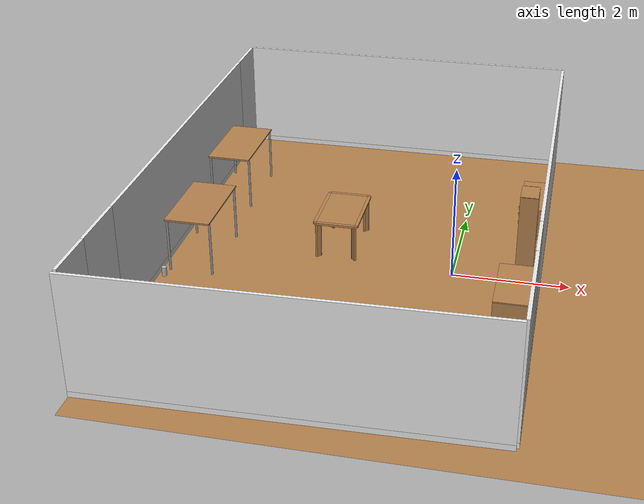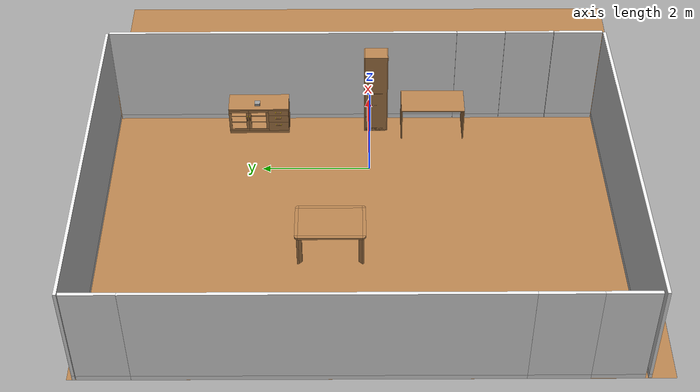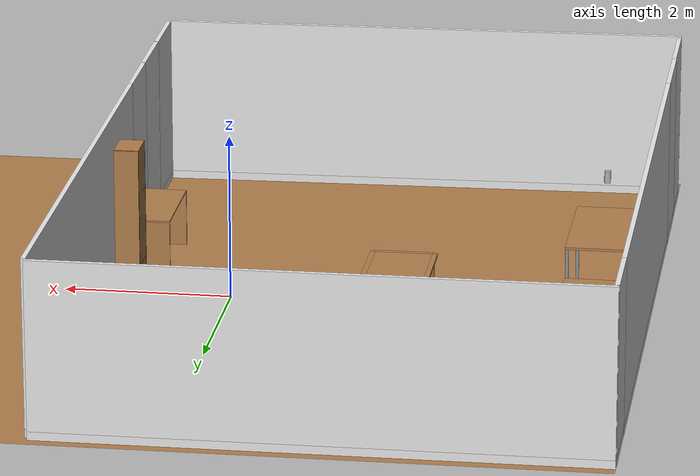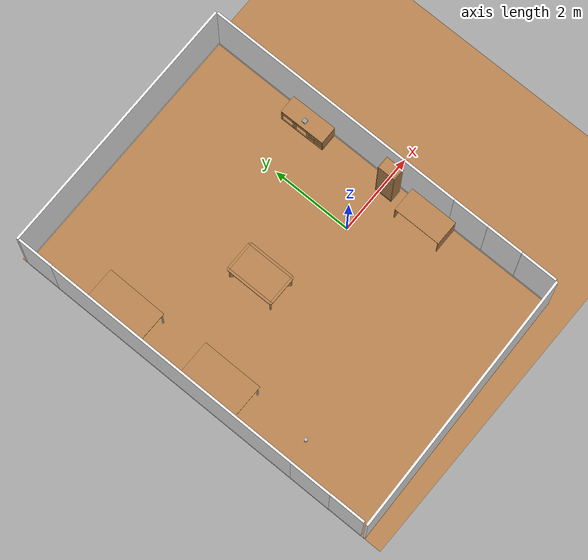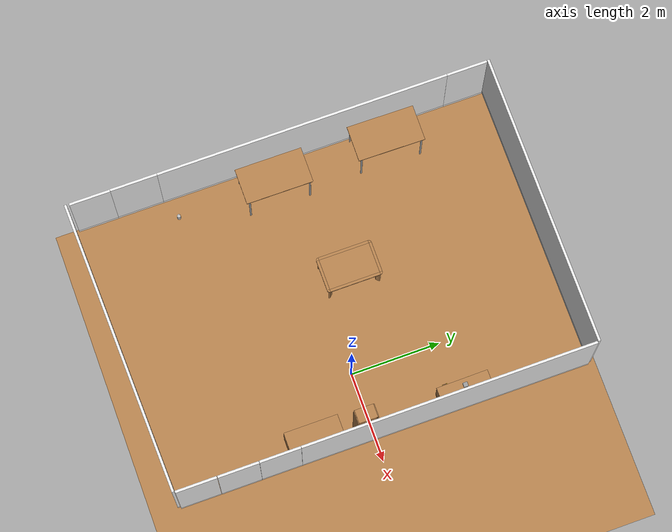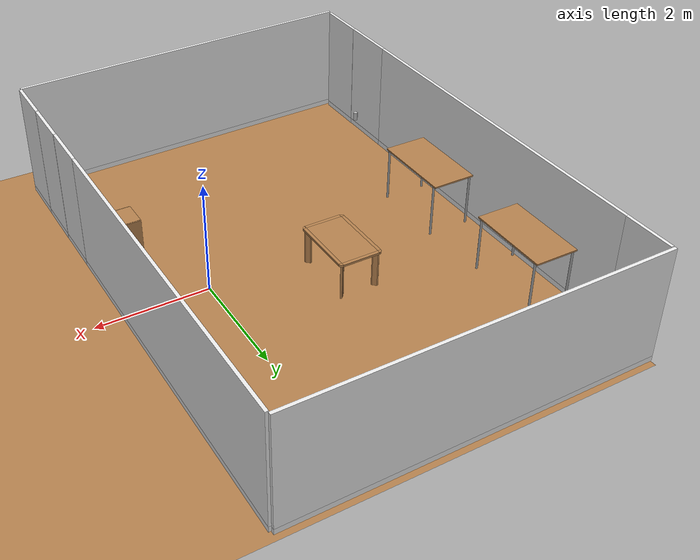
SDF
<sdf version="1.6">
 <world name="default">
  <light name="sun" type="directional">
   <pose>0 0 10 0 -0 0</pose>
   <diffuse>0.8 0.8 0.8 1</diffuse>
   <specular>0.2 0.2 0.2 1</specular>
   <attenuation>
    <range>1000</range>
    <constant>0.9</constant>
    <linear>0.01</linear>
    <quadratic>0.001</quadratic>
   </attenuation>
   <direction>-0.5 0.1 -0.9</direction>
  </light>
  <gravity>0 0 -9.8</gravity>
  <physics name="default_physics" default="0" type="ode">
   <max_step_size>0.001</max_step_size>
   <real_time_factor>1</real_time_factor>
   <real_time_update_rate>1000</real_time_update_rate>
  </physics>
  <scene><ambient>0.4 0.4 0.4 1</ambient><background>0.7 0.7 0.7 1</background><shadows>1</shadows></scene>
  <model name="wrc_ground_plane">
   <static>1</static>
   <link name="link">
    <collision name="collision">
     <geometry><plane><normal>0 0 1</normal><size>10 10</size></plane></geometry>
     <surface>
      <contact><collide_bitmask>65535</collide_bitmask></contact>
      <friction><ode><mu>100</mu><mu2>50</mu2></ode></friction>
     </surface>
    </collision>
    <visual name="visual">
     <cast_shadows>0</cast_shadows>
     <geometry><plane><normal>0 0 1</normal><size>10 10</size></plane></geometry>
     <material>
      <script><uri>model://wrc_ground_plane/materials/wood.material</uri><name>WRS/WoodFloor</name></script>
     </material>
    </visual>
   </link>
  </model>
  <magnetic_field>6e-06 2.3e-05 -4.2e-05</magnetic_field>
  <atmosphere type="adiabatic"/>
  <spherical_coordinates>
   <surface_model>EARTH_WGS84</surface_model>
   <latitude_deg>0</latitude_deg>
   <longitude_deg>0</longitude_deg>
   <elevation>0</elevation>
   <heading_deg>0</heading_deg>
  </spherical_coordinates>
  <model name="kitchen_table">
   <link name="link">
    <inertial>
     <mass>10</mass>
     <inertia><ixx>1</ixx><ixy>0</ixy><ixz>0</ixz><iyy>1</iyy><iyz>0</iyz><izz>1</izz></inertia>
    </inertial>
    <visual name="center_board">
     <pose>0 0 0.68 0 -0 0</pose>
     <geometry><box><size>0.68 1.13 0.04</size></box></geometry>
     <material>
      <script><uri>model://base_materials/wood/scripts/wood.material</uri><name>base_materials/wood</name></script>
     </material>
    </visual>
    <collision name="collision_center_board">
     <pose>0 0 0.68 0 -0 0</pose>
     <geometry><box><size>0.68 1.13 0.04</size></box></geometry>
    </collision>
    <visual name="front_board">
     <pose>0.37 0 0.68 0 -0 0</pose>
     <geometry><box><size>0.06 1.13 0.04</size></box></geometry>
     <material>
      <script><uri>model://base_materials/wood/scripts/wood.material</uri><name>base_materials/wood</name></script>
     </material>
    </visual>
    <collision name="collision_front_board">
     <pose>0.37 0 0.68 0 -0 0</pose>
     <geometry><box><size>0.06 1.13 0.04</size></box></geometry>
    </collision>
    <visual name="back_board">
     <pose>-0.37 0 0.68 0 -0 0</pose>
     <geometry><box><size>0.06 1.13 0.04</size></box></geometry>
     <material>
      <script><uri>model://base_materials/wood/scripts/wood.material</uri><name>base_materials/wood</name></script>
     </material>
    </visual>
    <collision name="collision_back_board">
     <pose>-0.37 0 0.68 0 -0 0</pose>
     <geometry><box><size>0.06 1.13 0.04</size></box></geometry>
    </collision>
    <visual name="right_board">
     <pose>0 0.595 0.68 0 -0 0</pose>
     <geometry><box><size>0.68 0.06 0.04</size></box></geometry>
     <material>
      <script><uri>model://base_materials/wood/scripts/wood.material</uri><name>base_materials/wood</name></script>
     </material>
    </visual>
    <collision name="collision_right_board">
     <pose>0 0.595 0.68 0 -0 0</pose>
     <geometry><box><size>0.68 0.06 0.04</size></box></geometry>
    </collision>
    <visual name="left_board">
     <pose>0 -0.595 0.68 0 -0 0</pose>
     <geometry><box><size>0.68 0.06 0.04</size></box></geometry>
     <material>
      <script><uri>model://base_materials/wood/scripts/wood.material</uri><name>base_materials/wood</name></script>
     </material>
    </visual>
    <collision name="collision_left_board">
     <pose>0 -0.595 0.68 0 -0 0</pose>
     <geometry><box><size>0.68 0.06 0.04</size></box></geometry>
    </collision>
    <visual name="front_right_corner_board">
     <pose>0.34 0.565 0.68 0 -0 0</pose>
     <geometry><cylinder><radius>0.06</radius><length>0.039</length></cylinder></geometry>
     <material>
      <script><uri>model://base_materials/wood/scripts/wood.material</uri><name>base_materials/wood</name></script>
     </material>
    </visual>
    <collision name="collision_front_right_corner_board">
     <pose>0.34 0.565 0.68 0 -0 0</pose>
     <geometry><cylinder><radius>0.06</radius><length>0.039</length></cylinder></geometry>
    </collision>
    <visual name="front_left_corner_board">
     <pose>0.34 -0.565 0.68 0 -0 0</pose>
     <geometry><cylinder><radius>0.06</radius><length>0.039</length></cylinder></geometry>
     <material>
      <script><uri>model://base_materials/wood/scripts/wood.material</uri><name>base_materials/wood</name></script>
     </material>
    </visual>
    <collision name="collision_front_left_corner_board">
     <pose>0.34 -0.565 0.68 0 -0 0</pose>
     <geometry><cylinder><radius>0.06</radius><length>0.039</length></cylinder></geometry>
    </collision>
    <visual name="front_back_right_corner_board">
     <pose>-0.34 0.565 0.68 0 -0 0</pose>
     <geometry><cylinder><radius>0.06</radius><length>0.039</length></cylinder></geometry>
     <material>
      <script><uri>model://base_materials/wood/scripts/wood.material</uri><name>base_materials/wood</name></script>
     </material>
    </visual>
    <collision name="collision_back_right_corner_board">
     <pose>-0.34 0.565 0.68 0 -0 0</pose>
     <geometry><cylinder><radius>0.06</radius><length>0.039</length></cylinder></geometry>
    </collision>
    <visual name="front_back_left_corner_board">
     <pose>-0.34 -0.565 0.68 0 -0 0</pose>
     <geometry><cylinder><radius>0.06</radius><length>0.039</length></cylinder></geometry>
     <material>
      <script><uri>model://base_materials/wood/scripts/wood.material</uri><name>base_materials/wood</name></script>
     </material>
    </visual>
    <collision name="collision_back_left_corner_board">
     <pose>-0.34 -0.565 0.68 0 -0 0</pose>
     <geometry><cylinder><radius>0.06</radius><length>0.039</length></cylinder></geometry>
    </collision>
    <visual name="front_left_corner_frame1">
     <pose>0.345858 -0.57086 0.33 0 -0 0</pose>
     <geometry><cylinder><radius>0.02</radius><length>0.66</length></cylinder></geometry>
     <material>
      <script><uri>model://base_materials/wood/scripts/wood.material</uri><name>base_materials/wood</name></script>
     </material>
    </visual>
    <collision name="collision_front_left_corner_frame1">
     <pose>0.345858 -0.57086 0.33 0 -0 0</pose>
     <geometry><cylinder><radius>0.02</radius><length>0.66</length></cylinder></geometry>
    </collision>
    <visual name="front_left_corner_frame2">
     <pose>0.317574 -0.54257 0.33 0 -0 0.7854</pose>
     <geometry><box><size>0.04 0.08 0.66</size></box></geometry>
     <material>
      <script><uri>model://base_materials/wood/scripts/wood.material</uri><name>base_materials/wood</name></script>
     </material>
    </visual>
    <collision name="collision_front_left_corner_frame2">
     <pose>0.317574 -0.54257 0.33 0 -0 0.7854</pose>
     <geometry><box><size>0.04 0.08 0.66</size></box></geometry>
    </collision>
    <visual name="front_left_corner_frame3">
     <pose>0.289289 -0.51429 0.33 0 -0 0</pose>
     <geometry><cylinder><radius>0.02</radius><length>0.66</length></cylinder></geometry>
     <material>
      <script><uri>model://base_materials/wood/scripts/wood.material</uri><name>base_materials/wood</name></script>
     </material>
    </visual>
    <collision name="collision_front_left_corner_frame3">
     <pose>0.289289 -0.51429 0.33 0 -0 0</pose>
     <geometry><cylinder><radius>0.02</radius><length>0.66</length></cylinder></geometry>
    </collision>
    <visual name="front_right_corner_frame1">
     <pose>0.345858 0.57086 0.33 0 -0 0</pose>
     <geometry><cylinder><radius>0.02</radius><length>0.66</length></cylinder></geometry>
     <material>
      <script><uri>model://base_materials/wood/scripts/wood.material</uri><name>base_materials/wood</name></script>
     </material>
    </visual>
    <collision name="collision_front_right_corner_frame1">
     <pose>0.345858 0.57086 0.33 0 -0 0</pose>
     <geometry><cylinder><radius>0.02</radius><length>0.66</length></cylinder></geometry>
    </collision>
    <visual name="front_right_corner_frame2">
     <pose>0.317574 0.54257 0.33 0 0 -0.7854</pose>
     <geometry><box><size>0.04 0.08 0.66</size></box></geometry>
     <material>
      <script><uri>model://base_materials/wood/scripts/wood.material</uri><name>base_materials/wood</name></script>
     </material>
    </visual>
    <collision name="collision_front_right_corner_frame2">
     <pose>0.317574 0.54257 0.33 0 0 -0.7854</pose>
     <geometry><box><size>0.04 0.08 0.66</size></box></geometry>
    </collision>
    <visual name="front_right_corner_frame3">
     <pose>0.289289 0.51429 0.33 0 -0 0</pose>
     <geometry><cylinder><radius>0.02</radius><length>0.66</length></cylinder></geometry>
     <material>
      <script><uri>model://base_materials/wood/scripts/wood.material</uri><name>base_materials/wood</name></script>
     </material>
    </visual>
    <collision name="collision_front_right_corner_frame3">
     <pose>0.289289 0.51429 0.33 0 -0 0</pose>
     <geometry><cylinder><radius>0.02</radius><length>0.66</length></cylinder></geometry>
    </collision>
    <visual name="back_left_corner_frame1">
     <pose>-0.345858 -0.57086 0.33 0 -0 0</pose>
     <geometry><cylinder><radius>0.02</radius><length>0.66</length></cylinder></geometry>
     <material>
      <script><uri>model://base_materials/wood/scripts/wood.material</uri><name>base_materials/wood</name></script>
     </material>
    </visual>
    <collision name="collision_back_left_corner_frame1">
     <pose>-0.345858 -0.57086 0.33 0 -0 0</pose>
     <geometry><cylinder><radius>0.02</radius><length>0.66</length></cylinder></geometry>
    </collision>
    <visual name="back_left_corner_frame2">
     <pose>-0.317574 -0.54257 0.33 0 0 -0.7854</pose>
     <geometry><box><size>0.04 0.08 0.66</size></box></geometry>
     <material>
      <script><uri>model://base_materials/wood/scripts/wood.material</uri><name>base_materials/wood</name></script>
     </material>
    </visual>
    <collision name="collision_back_left_corner_frame2">
     <pose>-0.317574 -0.54257 0.33 0 0 -0.7854</pose>
     <geometry><box><size>0.04 0.08 0.66</size></box></geometry>
    </collision>
    <visual name="back_left_corner_frame3">
     <pose>-0.289289 -0.51429 0.33 0 -0 0</pose>
     <geometry><cylinder><radius>0.02</radius><length>0.66</length></cylinder></geometry>
     <material>
      <script><uri>model://base_materials/wood/scripts/wood.material</uri><name>base_materials/wood</name></script>
     </material>
    </visual>
    <collision name="collision_back_left_corner_frame3">
     <pose>-0.289289 -0.51429 0.33 0 -0 0</pose>
     <geometry><cylinder><radius>0.02</radius><length>0.66</length></cylinder></geometry>
    </collision>
    <visual name="back_right_corner_frame1">
     <pose>-0.345858 0.57086 0.33 0 -0 0</pose>
     <geometry><cylinder><radius>0.02</radius><length>0.66</length></cylinder></geometry>
     <material>
      <script><uri>model://base_materials/wood/scripts/wood.material</uri><name>base_materials/wood</name></script>
     </material>
    </visual>
    <collision name="collision_back_right_corner_frame1">
     <pose>-0.345858 0.57086 0.33 0 -0 0</pose>
     <geometry><cylinder><radius>0.02</radius><length>0.66</length></cylinder></geometry>
    </collision>
    <visual name="back_right_corner_frame2">
     <pose>-0.317574 0.54257 0.33 0 -0 0.7854</pose>
     <geometry><box><size>0.04 0.08 0.66</size></box></geometry>
     <material>
      <script><uri>model://base_materials/wood/scripts/wood.material</uri><name>base_materials/wood</name></script>
     </material>
    </visual>
    <collision name="collision_back_right_corner_frame2">
     <pose>-0.317574 0.54257 0.33 0 -0 0.7854</pose>
     <geometry><box><size>0.04 0.08 0.66</size></box></geometry>
    </collision>
    <visual name="back_right_corner_frame3">
     <pose>-0.289289 0.51429 0.33 0 -0 0</pose>
     <geometry><cylinder><radius>0.02</radius><length>0.66</length></cylinder></geometry>
     <material>
      <script><uri>model://base_materials/wood/scripts/wood.material</uri><name>base_materials/wood</name></script>
     </material>
    </visual>
    <collision name="collision_back_right_corner_frame3">
     <pose>-0.289289 0.51429 0.33 0 -0 0</pose>
     <geometry><cylinder><radius>0.02</radius><length>0.66</length></cylinder></geometry>
    </collision>
    <velocity_decay><linear>0</linear><angular>0</angular></velocity_decay>
   </link>
   <static>1</static>
   <pose>-2.0884 0.705344 0 0 -0 0</pose>
  </model>
  <model name="full_wall_55_6475_2090">
   <link name="link">
    <inertial>
     <mass>50</mass>
     <inertia><ixx>1</ixx><ixy>0</ixy><ixz>0</ixz><iyy>1</iyy><iyz>0</iyz><izz>1</izz></inertia>
    </inertial>
    <visual name="bottom_frame">
     <pose>0 0 0.05 0 -0 0</pose>
     <geometry><box><size>0.055 6.475 0.1</size></box></geometry>
     <material>
      <script><uri>model://base_materials/color/scripts</uri><name>hsr_color/white</name></script>
     </material>
    </visual>
    <collision name="collision_bottom_frame">
     <pose>0 0 0.05 0 -0 0</pose>
     <geometry><box><size>0.055 6.475 0.1</size></box></geometry>
    </collision>
    <visual name="wall">
     <pose>0 0 1.095 0 -0 0</pose>
     <geometry><box><size>0.055 6.475 1.99</size></box></geometry>
     <material>
      <script>
       <uri>model://base_materials/wall/scripts</uri>
       <uri>model://base_materials/wall/textures</uri>
       <name>wall/white_noise</name>
      </script>
     </material>
    </visual>
    <collision name="collision_wall">
     <pose>0 0 1.095 0 -0 0</pose>
     <geometry><box><size>0.055 6.475 1.99</size></box></geometry>
    </collision>
    <velocity_decay><linear>0</linear><angular>0</angular></velocity_decay>
   </link>
   <static>1</static>
   <pose>-4.98133 0.698061 0 0 -0 0</pose>
  </model>
  <model name="full_wall_55_900_2090">
   <link name="link">
    <inertial>
     <mass>50</mass>
     <inertia><ixx>1</ixx><ixy>0</ixy><ixz>0</ixz><iyy>1</iyy><iyz>0</iyz><izz>1</izz></inertia>
    </inertial>
    <visual name="bottom_frame">
     <pose>0 0 0.05 0 -0 0</pose>
     <geometry><box><size>0.055 1.04 0.1</size></box></geometry>
     <material>
      <script><uri>model://base_materials/color/scripts</uri><name>hsr_color/white</name></script>
     </material>
    </visual>
    <collision name="collision_bottom_frame">
     <pose>0 0 0.05 0 -0 0</pose>
     <geometry><box><size>0.055 1.04 0.1</size></box></geometry>
    </collision>
    <visual name="wall">
     <pose>0 0 1.095 0 -0 0</pose>
     <geometry><box><size>0.055 1.04 1.99</size></box></geometry>
     <material>
      <script>
       <uri>model://base_materials/wall/scripts</uri>
       <uri>model://base_materials/wall/textures</uri>
       <name>wall/white_noise</name>
      </script>
     </material>
    </visual>
    <collision name="collision_wall">
     <pose>0 0 1.095 0 -0 0</pose>
     <geometry><box><size>0.055 1.04 1.99</size></box></geometry>
    </collision>
    <velocity_decay><linear>0</linear><angular>0</angular></velocity_decay>
   </link>
   <static>1</static>
   <pose>-4.98186 -3.05819 0 0 -0 0</pose>
  </model>
  <model name="full_wall_55_900_2090_0">
   <link name="link">
    <inertial>
     <mass>50</mass>
     <inertia><ixx>1</ixx><ixy>0</ixy><ixz>0</ixz><iyy>1</iyy><iyz>0</iyz><izz>1</izz></inertia>
    </inertial>
    <visual name="bottom_frame">
     <pose>0 0 0.05 0 -0 0</pose>
     <geometry><box><size>0.055 0.9 0.1</size></box></geometry>
     <material>
      <script><uri>model://base_materials/color/scripts</uri><name>hsr_color/white</name></script>
     </material>
    </visual>
    <collision name="collision_bottom_frame">
     <pose>0 0 0.05 0 -0 0</pose>
     <geometry><box><size>0.055 0.9 0.1</size></box></geometry>
    </collision>
    <visual name="wall">
     <pose>0 0 1.095 0 -0 0</pose>
     <geometry><box><size>0.055 0.9 1.99</size></box></geometry>
     <material>
      <script>
       <uri>model://base_materials/wall/scripts</uri>
       <uri>model://base_materials/wall/textures</uri>
       <name>wall/white_noise</name>
      </script>
     </material>
    </visual>
    <collision name="collision_wall">
     <pose>0 0 1.095 0 -0 0</pose>
     <geometry><box><size>0.055 0.9 1.99</size></box></geometry>
    </collision>
    <velocity_decay><linear>0</linear><angular>0</angular></velocity_decay>
   </link>
   <static>1</static>
   <pose>-4.97819 -4.022 0 0 -0 0</pose>
  </model>
  <model name="full_wall_55_6475_2090_0">
   <link name="link">
    <inertial>
     <mass>50</mass>
     <inertia><ixx>1</ixx><ixy>0</ixy><ixz>0</ixz><iyy>1</iyy><iyz>0</iyz><izz>1</izz></inertia>
    </inertial>
    <visual name="bottom_frame">
     <pose>0 0 0.05 0 -0 0</pose>
     <geometry><box><size>0.055 6.475 0.1</size></box></geometry>
     <material>
      <script><uri>model://base_materials/color/scripts</uri><name>hsr_color/white</name></script>
     </material>
    </visual>
    <collision name="collision_bottom_frame">
     <pose>0 0 0.05 0 -0 0</pose>
     <geometry><box><size>0.055 6.475 0.1</size></box></geometry>
    </collision>
    <visual name="wall">
     <pose>0 0 1.095 0 -0 0</pose>
     <geometry><box><size>0.055 6.475 1.99</size></box></geometry>
     <material>
      <script>
       <uri>model://base_materials/wall/scripts</uri>
       <uri>model://base_materials/wall/textures</uri>
       <name>wall/white_noise</name>
      </script>
     </material>
    </visual>
    <collision name="collision_wall">
     <pose>0 0 1.095 0 -0 0</pose>
     <geometry><box><size>0.055 6.475 1.99</size></box></geometry>
    </collision>
    <velocity_decay><linear>0</linear><angular>0</angular></velocity_decay>
   </link>
   <static>1</static>
   <pose>-1.76352 -4.46985 0 0 -0 1.59642</pose>
  </model>
  <model name="full_wall_55_900_2090_1">
   <link name="link">
    <inertial>
     <mass>50</mass>
     <inertia><ixx>1</ixx><ixy>0</ixy><ixz>0</ixz><iyy>1</iyy><iyz>0</iyz><izz>1</izz></inertia>
    </inertial>
    <visual name="bottom_frame">
     <pose>0 0 0.05 0 -0 0</pose>
     <geometry><box><size>0.055 0.9 0.1</size></box></geometry>
     <material>
      <script><uri>model://base_materials/color/scripts</uri><name>hsr_color/white</name></script>
     </material>
    </visual>
    <collision name="collision_bottom_frame">
     <pose>0 0 0.05 0 -0 0</pose>
     <geometry><box><size>0.055 0.9 0.1</size></box></geometry>
    </collision>
    <visual name="wall">
     <pose>0 0 1.095 0 -0 0</pose>
     <geometry><box><size>0.055 0.9 1.99</size></box></geometry>
     <material>
      <script>
       <uri>model://base_materials/wall/scripts</uri>
       <uri>model://base_materials/wall/textures</uri>
       <name>wall/white_noise</name>
      </script>
     </material>
    </visual>
    <collision name="collision_wall">
     <pose>0 0 1.095 0 -0 0</pose>
     <geometry><box><size>0.055 0.9 1.99</size></box></geometry>
    </collision>
    <velocity_decay><linear>0</linear><angular>0</angular></velocity_decay>
   </link>
   <static>1</static>
   <pose>1.48612 -3.90071 0 0 -0 0</pose>
  </model>
  <model name="full_wall_55_900_2090_2">
   <link name="link">
    <inertial>
     <mass>50</mass>
     <inertia><ixx>1</ixx><ixy>0</ixy><ixz>0</ixz><iyy>1</iyy><iyz>0</iyz><izz>1</izz></inertia>
    </inertial>
    <visual name="bottom_frame">
     <pose>0 0 0.05 0 -0 0</pose>
     <geometry><box><size>0.055 0.9 0.1</size></box></geometry>
     <material>
      <script><uri>model://base_materials/color/scripts</uri><name>hsr_color/white</name></script>
     </material>
    </visual>
    <collision name="collision_bottom_frame">
     <pose>0 0 0.05 0 -0 0</pose>
     <geometry><box><size>0.055 0.9 0.1</size></box></geometry>
    </collision>
    <visual name="wall">
     <pose>0 0 1.095 0 -0 0</pose>
     <geometry><box><size>0.055 0.9 1.99</size></box></geometry>
     <material>
      <script>
       <uri>model://base_materials/wall/scripts</uri>
       <uri>model://base_materials/wall/textures</uri>
       <name>wall/white_noise</name>
      </script>
     </material>
    </visual>
    <collision name="collision_wall">
     <pose>0 0 1.095 0 -0 0</pose>
     <geometry><box><size>0.055 0.9 1.99</size></box></geometry>
    </collision>
    <velocity_decay><linear>0</linear><angular>0</angular></velocity_decay>
   </link>
   <static>1</static>
   <pose>1.48699 -2.99289 0 0 -0 0</pose>
  </model>
  <model name="full_wall_55_900_2090_3">
   <link name="link">
    <inertial>
     <mass>50</mass>
     <inertia><ixx>1</ixx><ixy>0</ixy><ixz>0</ixz><iyy>1</iyy><iyz>0</iyz><izz>1</izz></inertia>
    </inertial>
    <visual name="bottom_frame">
     <pose>0 0 0.05 0 -0 0</pose>
     <geometry><box><size>0.055 0.9 0.1</size></box></geometry>
     <material>
      <script><uri>model://base_materials/color/scripts</uri><name>hsr_color/white</name></script>
     </material>
    </visual>
    <collision name="collision_bottom_frame">
     <pose>0 0 0.05 0 -0 0</pose>
     <geometry><box><size>0.055 0.9 0.1</size></box></geometry>
    </collision>
    <visual name="wall">
     <pose>0 0 1.095 0 -0 0</pose>
     <geometry><box><size>0.055 0.9 1.99</size></box></geometry>
     <material>
      <script>
       <uri>model://base_materials/wall/scripts</uri>
       <uri>model://base_materials/wall/textures</uri>
       <name>wall/white_noise</name>
      </script>
     </material>
    </visual>
    <collision name="collision_wall">
     <pose>0 0 1.095 0 -0 0</pose>
     <geometry><box><size>0.055 0.9 1.99</size></box></geometry>
    </collision>
    <velocity_decay><linear>0</linear><angular>0</angular></velocity_decay>
   </link>
   <static>1</static>
   <pose>1.48439 -2.08933 0 0 -0 0</pose>
  </model>
  <model name="full_wall_55_6475_2090_1">
   <link name="link">
    <inertial>
     <mass>50</mass>
     <inertia><ixx>1</ixx><ixy>0</ixy><ixz>0</ixz><iyy>1</iyy><iyz>0</iyz><izz>1</izz></inertia>
    </inertial>
    <visual name="bottom_frame">
     <pose>0 0 0.05 0 -0 0</pose>
     <geometry><box><size>0.055 6.475 0.1</size></box></geometry>
     <material>
      <script><uri>model://base_materials/color/scripts</uri><name>hsr_color/white</name></script>
     </material>
    </visual>
    <collision name="collision_bottom_frame">
     <pose>0 0 0.05 0 -0 0</pose>
     <geometry><box><size>0.055 6.475 0.1</size></box></geometry>
    </collision>
    <visual name="wall">
     <pose>0 0 1.095 0 -0 0</pose>
     <geometry><box><size>0.055 6.475 1.99</size></box></geometry>
     <material>
      <script>
       <uri>model://base_materials/wall/scripts</uri>
       <uri>model://base_materials/wall/textures</uri>
       <name>wall/white_noise</name>
      </script>
     </material>
    </visual>
    <collision name="collision_wall">
     <pose>0 0 1.095 0 -0 0</pose>
     <geometry><box><size>0.055 6.475 1.99</size></box></geometry>
    </collision>
    <velocity_decay><linear>0</linear><angular>0</angular></velocity_decay>
   </link>
   <static>1</static>
   <pose>1.48469 1.60041 0 0 -0 0</pose>
  </model>
  <model name="full_wall_55_900_2090_4">
   <link name="link">
    <inertial>
     <mass>50</mass>
     <inertia><ixx>1</ixx><ixy>0</ixy><ixz>0</ixz><iyy>1</iyy><iyz>0</iyz><izz>1</izz></inertia>
    </inertial>
    <visual name="bottom_frame">
     <pose>0 0 0.05 0 -0 0</pose>
     <geometry><box><size>0.055 0.9 0.1</size></box></geometry>
     <material>
      <script><uri>model://base_materials/color/scripts</uri><name>hsr_color/white</name></script>
     </material>
    </visual>
    <collision name="collision_bottom_frame">
     <pose>0 0 0.05 0 -0 0</pose>
     <geometry><box><size>0.055 0.9 0.1</size></box></geometry>
    </collision>
    <visual name="wall">
     <pose>0 0 1.095 0 -0 0</pose>
     <geometry><box><size>0.055 0.9 1.99</size></box></geometry>
     <material>
      <script>
       <uri>model://base_materials/wall/scripts</uri>
       <uri>model://base_materials/wall/textures</uri>
       <name>wall/white_noise</name>
      </script>
     </material>
    </visual>
    <collision name="collision_wall">
     <pose>0 0 1.095 0 -0 0</pose>
     <geometry><box><size>0.055 0.9 1.99</size></box></geometry>
    </collision>
    <velocity_decay><linear>0</linear><angular>0</angular></velocity_decay>
   </link>
   <static>1</static>
   <pose>-4.9797 4.38402 0 0 -0 0</pose>
  </model>
  <model name="full_wall_55_6475_2090_2">
   <link name="link">
    <inertial>
     <mass>50</mass>
     <inertia><ixx>1</ixx><ixy>0</ixy><ixz>0</ixz><iyy>1</iyy><iyz>0</iyz><izz>1</izz></inertia>
    </inertial>
    <visual name="bottom_frame">
     <pose>0 0 0.05 0 -0 0</pose>
     <geometry><box><size>0.055 6.475 0.1</size></box></geometry>
     <material>
      <script><uri>model://base_materials/color/scripts</uri><name>hsr_color/white</name></script>
     </material>
    </visual>
    <collision name="collision_bottom_frame">
     <pose>0 0 0.05 0 -0 0</pose>
     <geometry><box><size>0.055 6.475 0.1</size></box></geometry>
    </collision>
    <visual name="wall">
     <pose>0 0 1.095 0 -0 0</pose>
     <geometry><box><size>0.055 6.475 1.99</size></box></geometry>
     <material>
      <script>
       <uri>model://base_materials/wall/scripts</uri>
       <uri>model://base_materials/wall/textures</uri>
       <name>wall/white_noise</name>
      </script>
     </material>
    </visual>
    <collision name="collision_wall">
     <pose>0 0 1.095 0 -0 0</pose>
     <geometry><box><size>0.055 6.475 1.99</size></box></geometry>
    </collision>
    <velocity_decay><linear>0</linear><angular>0</angular></velocity_decay>
   </link>
   <static>1</static>
   <pose>-1.76449 4.87676 0 0 0 -1.57017</pose>
  </model>
  <model name="table">
   <static>1</static>
   <link name="link">
    <collision name="surface">
     <pose>0 0 1 0 -0 0</pose>
     <geometry><box><size>1.5 0.8 0.03</size></box></geometry>
     <surface><friction><ode><mu>0.6</mu><mu2>0.6</mu2></ode></friction></surface>
    </collision>
    <visual name="visual1">
     <pose>0 0 1 0 -0 0</pose>
     <geometry><box><size>1.5 0.8 0.03</size></box></geometry>
     <material>
      <script><uri>file://media/materials/scripts/gazebo.material</uri><name>Gazebo/Wood</name></script>
     </material>
    </visual>
    <collision name="front_left_leg">
     <pose>0.68 0.38 0.5 0 -0 0</pose>
     <geometry><cylinder><radius>0.02</radius><length>1</length></cylinder></geometry>
    </collision>
    <visual name="front_left_leg">
     <pose>0.68 0.38 0.5 0 -0 0</pose>
     <geometry><cylinder><radius>0.02</radius><length>1</length></cylinder></geometry>
     <material>
      <script><uri>file://media/materials/scripts/gazebo.material</uri><name>Gazebo/Grey</name></script>
     </material>
    </visual>
    <collision name="front_right_leg">
     <pose>0.68 -0.38 0.5 0 -0 0</pose>
     <geometry><cylinder><radius>0.02</radius><length>1</length></cylinder></geometry>
    </collision>
    <visual name="front_right_leg">
     <pose>0.68 -0.38 0.5 0 -0 0</pose>
     <geometry><cylinder><radius>0.02</radius><length>1</length></cylinder></geometry>
     <material>
      <script><uri>file://media/materials/scripts/gazebo.material</uri><name>Gazebo/Grey</name></script>
     </material>
    </visual>
    <collision name="back_right_leg">
     <pose>-0.68 -0.38 0.5 0 -0 0</pose>
     <geometry><cylinder><radius>0.02</radius><length>1</length></cylinder></geometry>
    </collision>
    <visual name="back_right_leg">
     <pose>-0.68 -0.38 0.5 0 -0 0</pose>
     <geometry><cylinder><radius>0.02</radius><length>1</length></cylinder></geometry>
     <material>
      <script><uri>file://media/materials/scripts/gazebo.material</uri><name>Gazebo/Grey</name></script>
     </material>
    </visual>
    <collision name="back_left_leg">
     <pose>-0.68 0.38 0.5 0 -0 0</pose>
     <geometry><cylinder><radius>0.02</radius><length>1</length></cylinder></geometry>
    </collision>
    <visual name="back_left_leg">
     <pose>-0.68 0.38 0.5 0 -0 0</pose>
     <geometry><cylinder><radius>0.02</radius><length>1</length></cylinder></geometry>
     <material>
      <script><uri>file://media/materials/scripts/gazebo.material</uri><name>Gazebo/Grey</name></script>
     </material>
    </visual>
   </link>
   <pose>-4.51458 2.4162 0 0 0 -1.58412</pose>
  </model>
  <model name="high_shelf">
   <link name="link">
    <inertial>
     <mass>5</mass>
     <inertia><ixx>1</ixx><ixy>0</ixy><ixz>0</ixz><iyy>1</iyy><iyz>0</iyz><izz>1</izz></inertia>
    </inertial>
    <visual name="left_board">
     <pose>-0.1475 0.009 0.898 0 -0 0</pose>
     <geometry><box><size>0.295 0.018 1.796</size></box></geometry>
     <material>
      <script>
       <uri>model://base_materials/wood/scripts</uri>
       <uri>model://base_materials/wood/textures</uri>
       <name>base_materials/light_wood</name>
      </script>
     </material>
    </visual>
    <collision name="collision_left_board">
     <pose>-0.1475 0.009 0.898 0 -0 0</pose>
     <geometry><box><size>0.295 0.018 1.796</size></box></geometry>
    </collision>
    <visual name="right_board">
     <pose>-0.1475 0.441 0.898 0 -0 0</pose>
     <geometry><box><size>0.295 0.018 1.796</size></box></geometry>
     <material>
      <script>
       <uri>model://base_materials/wood/scripts</uri>
       <uri>model://base_materials/wood/textures</uri>
       <name>base_materials/light_wood</name>
      </script>
     </material>
    </visual>
    <collision name="collision_right_board">
     <pose>-0.1475 0.441 0.898 0 -0 0</pose>
     <geometry><box><size>0.295 0.018 1.796</size></box></geometry>
    </collision>
    <visual name="top_board">
     <pose>-0.1475 0.225 1.7825 0 -0 0</pose>
     <geometry><box><size>0.295 0.414 0.035</size></box></geometry>
     <material>
      <script>
       <uri>model://base_materials/wood/scripts</uri>
       <uri>model://base_materials/wood/textures</uri>
       <name>base_materials/light_wood</name>
      </script>
     </material>
    </visual>
    <collision name="collision_top_board">
     <pose>-0.1475 0.225 1.7825 0 -0 0</pose>
     <geometry><box><size>0.295 0.414 0.035</size></box></geometry>
    </collision>
    <visual name="1st_shelf">
     <pose>-0.162 0.225 1.51 0 -0 0</pose>
     <geometry><box><size>0.266 0.414 0.018</size></box></geometry>
     <material>
      <script>
       <uri>model://base_materials/wood/scripts</uri>
       <uri>model://base_materials/wood/textures</uri>
       <name>base_materials/light_wood</name>
      </script>
     </material>
    </visual>
    <collision name="collision_1st_shelf">
     <pose>-0.162 0.225 1.51 0 -0 0</pose>
     <geometry><box><size>0.266 0.414 0.018</size></box></geometry>
    </collision>
    <visual name="2nd_shelf">
     <pose>-0.162 0.225 1.22 0 -0 0</pose>
     <geometry><box><size>0.266 0.414 0.018</size></box></geometry>
     <material>
      <script>
       <uri>model://base_materials/wood/scripts</uri>
       <uri>model://base_materials/wood/textures</uri>
       <name>base_materials/light_wood</name>
      </script>
     </material>
    </visual>
    <collision name="collision_2nd_shelf">
     <pose>-0.162 0.225 1.22 0 -0 0</pose>
     <geometry><box><size>0.266 0.414 0.018</size></box></geometry>
    </collision>
    <visual name="3rd_shelf">
     <pose>-0.162 0.225 0.93 0 -0 0</pose>
     <geometry><box><size>0.266 0.414 0.018</size></box></geometry>
     <material>
      <script>
       <uri>model://base_materials/wood/scripts</uri>
       <uri>model://base_materials/wood/textures</uri>
       <name>base_materials/light_wood</name>
      </script>
     </material>
    </visual>
    <collision name="collision_3rd_shelf">
     <pose>-0.162 0.225 0.93 0 -0 0</pose>
     <geometry><box><size>0.266 0.414 0.018</size></box></geometry>
    </collision>
    <visual name="4th_shelf">
     <pose>-0.162 0.225 0.65 0 -0 0</pose>
     <geometry><box><size>0.266 0.414 0.018</size></box></geometry>
     <material>
      <script>
       <uri>model://base_materials/wood/scripts</uri>
       <uri>model://base_materials/wood/textures</uri>
       <name>base_materials/light_wood</name>
      </script>
     </material>
    </visual>
    <collision name="collision_4th_shelf">
     <pose>-0.162 0.225 0.65 0 -0 0</pose>
     <geometry><box><size>0.266 0.414 0.018</size></box></geometry>
    </collision>
    <visual name="5th_shelf">
     <pose>-0.162 0.225 0.36 0 -0 0</pose>
     <geometry><box><size>0.266 0.414 0.018</size></box></geometry>
     <material>
      <script>
       <uri>model://base_materials/wood/scripts</uri>
       <uri>model://base_materials/wood/textures</uri>
       <name>base_materials/light_wood</name>
      </script>
     </material>
    </visual>
    <collision name="collision_5th_shelf">
     <pose>-0.162 0.225 0.36 0 -0 0</pose>
     <geometry><box><size>0.266 0.414 0.018</size></box></geometry>
    </collision>
    <visual name="bottom_board">
     <pose>-0.1475 0.225 0.035 0 -0 0</pose>
     <geometry><box><size>0.295 0.414 0.07</size></box></geometry>
     <material>
      <script>
       <uri>model://base_materials/wood/scripts</uri>
       <uri>model://base_materials/wood/textures</uri>
       <name>base_materials/light_wood</name>
      </script>
     </material>
    </visual>
    <collision name="collision_bottom_board">
     <pose>-0.1475 0.225 0.035 0 -0 0</pose>
     <geometry><box><size>0.295 0.414 0.07</size></box></geometry>
    </collision>
    <visual name="back_board">
     <pose>-0.286 0.225 0.898 0 -0 0</pose>
     <geometry><box><size>0.018 0.414 1.796</size></box></geometry>
     <material>
      <script>
       <uri>model://base_materials/wood/scripts</uri>
       <uri>model://base_materials/wood/textures</uri>
       <name>base_materials/light_wood</name>
      </script>
     </material>
    </visual>
    <collision name="collision_back_board">
     <pose>-0.286 0.225 0.898 0 -0 0</pose>
     <geometry><box><size>0.018 0.414 1.796</size></box></geometry>
    </collision>
    <velocity_decay><linear>0</linear><angular>0</angular></velocity_decay>
   </link>
   <static>1</static>
   <pose>1.37619 -0.357647 0 0 -0 0</pose>
  </model>
  <model name="living_sideboard">
   <link name="link">
    <inertial>
     <mass>10</mass>
     <inertia><ixx>1</ixx><ixy>0</ixy><ixz>0</ixz><iyy>1</iyy><iyz>0</iyz><izz>1</izz></inertia>
    </inertial>
    <visual name="left_board">
     <pose>-0.23 0.01 0.3375 0 -0 0</pose>
     <geometry><box><size>0.42 0.02 0.495</size></box></geometry>
     <material>
      <script><uri>model://base_materials/wood/scripts/wood.material</uri><name>base_materials/wood</name></script>
     </material>
    </visual>
    <collision name="collision_left_board">
     <pose>-0.23 0.01 0.3375 0 -0 0</pose>
     <geometry><box><size>0.42 0.02 0.495</size></box></geometry>
    </collision>
    <visual name="back_board">
     <pose>-0.42 0.575 0.2925 0 -0 0</pose>
     <geometry><box><size>0.02 1.11 0.585</size></box></geometry>
     <material>
      <script><uri>model://base_materials/wood/scripts/wood.material</uri><name>base_materials/wood</name></script>
     </material>
    </visual>
    <collision name="collision_back_board">
     <pose>-0.42 0.575 0.2925 0 -0 0</pose>
     <geometry><box><size>0.02 1.11 0.585</size></box></geometry>
    </collision>
    <visual name="right_board">
     <pose>-0.23 1.14 0.3375 0 -0 0</pose>
     <geometry><box><size>0.42 0.02 0.495</size></box></geometry>
     <material>
      <script><uri>model://base_materials/wood/scripts/wood.material</uri><name>base_materials/wood</name></script>
     </material>
    </visual>
    <collision name="collision_right_board">
     <pose>-0.23 1.14 0.3375 0 -0 0</pose>
     <geometry><box><size>0.42 0.02 0.495</size></box></geometry>
    </collision>
    <visual name="center_vertical_board1">
     <pose>-0.23 0.74 0.3375 0 -0 0</pose>
     <geometry><box><size>0.42 0.02 0.495</size></box></geometry>
     <material>
      <script><uri>model://base_materials/wood/scripts/wood.material</uri><name>base_materials/wood</name></script>
     </material>
    </visual>
    <collision name="collision_center_vertical_board1">
     <pose>-0.23 0.74 0.3375 0 -0 0</pose>
     <geometry><box><size>0.42 0.02 0.495</size></box></geometry>
    </collision>
    <visual name="top_board">
     <pose>-0.22 0.575 0.6 0 -0 0</pose>
     <geometry><box><size>0.44 1.15 0.03</size></box></geometry>
     <material>
      <script><uri>model://base_materials/wood/scripts/wood.material</uri><name>base_materials/wood</name></script>
     </material>
    </visual>
    <collision name="collision_top_board">
     <pose>-0.22 0.575 0.6 0 -0 0</pose>
     <geometry><box><size>0.44 1.15 0.03</size></box></geometry>
    </collision>
    <visual name="bottom_board">
     <pose>-0.23 0.575 0.045 0 -0 0</pose>
     <geometry><box><size>0.42 1.15 0.09</size></box></geometry>
     <material>
      <script><uri>model://base_materials/wood/scripts/wood.material</uri><name>base_materials/wood</name></script>
     </material>
    </visual>
    <collision name="collision_bottom_board">
     <pose>-0.23 0.575 0.045 0 -0 0</pose>
     <geometry><box><size>0.42 1.15 0.09</size></box></geometry>
    </collision>
    <visual name="1st_shelf">
     <pose>-0.225 0.37 0.259 0 -0 0</pose>
     <geometry><box><size>0.36 0.72 0.018</size></box></geometry>
     <material>
      <script><uri>model://base_materials/wood/scripts/wood.material</uri><name>base_materials/wood</name></script>
     </material>
    </visual>
    <collision name="collision_1st_shelf">
     <pose>-0.225 0.37 0.259 0 -0 0</pose>
     <geometry><box><size>0.36 0.72 0.018</size></box></geometry>
    </collision>
    <visual name="2nd_shelf">
     <pose>-0.225 0.37 0.407 0 -0 0</pose>
     <geometry><box><size>0.36 0.72 0.018</size></box></geometry>
     <material>
      <script><uri>model://base_materials/wood/scripts/wood.material</uri><name>base_materials/wood</name></script>
     </material>
    </visual>
    <collision name="collision_2nd_shelf">
     <pose>-0.225 0.37 0.407 0 -0 0</pose>
     <geometry><box><size>0.36 0.72 0.018</size></box></geometry>
    </collision>
    <visual name="1st_drawer">
     <pose>-0.2025 0.95 0.52 0 -0 0</pose>
     <geometry><box><size>0.405 0.38 0.13</size></box></geometry>
     <material>
      <script><uri>model://base_materials/wood/scripts/wood.material</uri><name>base_materials/wood</name></script>
     </material>
    </visual>
    <collision name="collision_1st_drawer">
     <pose>-0.2025 0.95 0.52 0 -0 0</pose>
     <geometry><box><size>0.405 0.38 0.13</size></box></geometry>
    </collision>
    <visual name="1st_drawer_handle_l1">
     <pose>0.015 0.9015 0.535 3.14159 1.57079 3.14159</pose>
     <geometry><cylinder><radius>0.006</radius><length>0.03</length></cylinder></geometry>
     <material>
      <ambient>1 0.84314 0 1</ambient>
      <diffuse>1 0.84314 0 1</diffuse>
      <specular>0.1 0.1 0.1 1</specular>
     </material>
    </visual>
    <collision name="collision_1st_drawer_handle_l1">
     <pose>0.015 0.9015 0.535 3.14159 1.57079 3.14159</pose>
     <geometry><cylinder><radius>0.006</radius><length>0.03</length></cylinder></geometry>
    </collision>
    <visual name="1st_drawer_handle_l2">
     <pose>0.03 0.9015 0.535 0 -0 0</pose>
     <geometry><sphere><radius>0.006</radius></sphere></geometry>
     <material>
      <ambient>1 0.84314 0 1</ambient>
      <diffuse>1 0.84314 0 1</diffuse>
      <specular>0.1 0.1 0.1 1</specular>
     </material>
    </visual>
    <collision name="collision_1st_drawer_handle_l2">
     <pose>0.03 0.9015 0.535 0 -0 0</pose>
     <geometry><sphere><radius>0.006</radius></sphere></geometry>
    </collision>
    <visual name="1st_drawer_handle_r1">
     <pose>0.015 0.9985 0.535 3.14159 1.57079 3.14159</pose>
     <geometry><cylinder><radius>0.006</radius><length>0.03</length></cylinder></geometry>
     <material>
      <ambient>1 0.84314 0 1</ambient>
      <diffuse>1 0.84314 0 1</diffuse>
      <specular>0.1 0.1 0.1 1</specular>
     </material>
    </visual>
    <collision name="collision_1st_drawer_handle_r1">
     <pose>0.015 0.9985 0.535 3.14159 1.57079 3.14159</pose>
     <geometry><cylinder><radius>0.006</radius><length>0.03</length></cylinder></geometry>
    </collision>
    <visual name="1st_drawer_handle_r2">
     <pose>0.03 0.9985 0.535 0 -0 0</pose>
     <geometry><sphere><radius>0.006</radius></sphere></geometry>
     <material>
      <ambient>1 0.84314 0 1</ambient>
      <diffuse>1 0.84314 0 1</diffuse>
      <specular>0.1 0.1 0.1 1</specular>
     </material>
    </visual>
    <collision name="collision_1st_drawer_handle_r2">
     <pose>0.03 0.9985 0.535 0 -0 0</pose>
     <geometry><sphere><radius>0.006</radius></sphere></geometry>
    </collision>
    <visual name="1st_drawer_handle_center">
     <pose>0.03 0.95 0.535 1.5708 -0 0</pose>
     <geometry><cylinder><radius>0.006</radius><length>0.097</length></cylinder></geometry>
     <material>
      <script><uri>model://base_materials/wood/scripts/wood.material</uri><name>base_materials/wood</name></script>
     </material>
    </visual>
    <collision name="collision_1st_drawer_handle_center">
     <pose>0.03 0.95 0.535 1.5708 -0 0</pose>
     <geometry><cylinder><radius>0.006</radius><length>0.097</length></cylinder></geometry>
    </collision>
    <visual name="2nd_drawer">
     <pose>-0.2025 0.95 0.37 0 -0 0</pose>
     <geometry><box><size>0.405 0.38 0.17</size></box></geometry>
     <material>
      <script><uri>model://base_materials/wood/scripts/wood.material</uri><name>base_materials/wood</name></script>
     </material>
    </visual>
    <collision name="collision_2nd_drawer">
     <pose>-0.2025 0.95 0.37 0 -0 0</pose>
     <geometry><box><size>0.405 0.38 0.17</size></box></geometry>
    </collision>
    <visual name="2nd_drawer_handle_l1">
     <pose>0.015 0.9015 0.405 3.14159 1.57079 3.14159</pose>
     <geometry><cylinder><radius>0.006</radius><length>0.03</length></cylinder></geometry>
     <material>
      <ambient>1 0.84314 0 1</ambient>
      <diffuse>1 0.84314 0 1</diffuse>
      <specular>0.1 0.1 0.1 1</specular>
     </material>
    </visual>
    <collision name="collision_2nd_drawer_handle_l1">
     <pose>0.015 0.9015 0.405 3.14159 1.57079 3.14159</pose>
     <geometry><cylinder><radius>0.006</radius><length>0.03</length></cylinder></geometry>
    </collision>
    <visual name="2nd_drawer_handle_l2">
     <pose>0.03 0.9015 0.405 0 -0 0</pose>
     <geometry><sphere><radius>0.006</radius></sphere></geometry>
     <material>
      <ambient>1 0.84314 0 1</ambient>
      <diffuse>1 0.84314 0 1</diffuse>
      <specular>0.1 0.1 0.1 1</specular>
     </material>
    </visual>
    <collision name="collision_2nd_drawer_handle_l2">
     <pose>0.03 0.9015 0.405 0 -0 0</pose>
     <geometry><sphere><radius>0.006</radius></sphere></geometry>
    </collision>
    <visual name="2nd_drawer_handle_r1">
     <pose>0.015 0.9985 0.405 3.14159 1.57079 3.14159</pose>
     <geometry><cylinder><radius>0.006</radius><length>0.03</length></cylinder></geometry>
     <material>
      <ambient>1 0.84314 0 1</ambient>
      <diffuse>1 0.84314 0 1</diffuse>
      <specular>0.1 0.1 0.1 1</specular>
     </material>
    </visual>
    <collision name="collision_2nd_drawer_handle_r1">
     <pose>0.015 0.9985 0.405 3.14159 1.57079 3.14159</pose>
     <geometry><cylinder><radius>0.006</radius><length>0.03</length></cylinder></geometry>
    </collision>
    <visual name="2nd_drawer_handle_r2">
     <pose>0.03 0.9985 0.405 0 -0 0</pose>
     <geometry><sphere><radius>0.006</radius></sphere></geometry>
     <material>
      <ambient>1 0.84314 0 1</ambient>
      <diffuse>1 0.84314 0 1</diffuse>
      <specular>0.1 0.1 0.1 1</specular>
     </material>
    </visual>
    <collision name="collision_2nd_drawer_handle_r2">
     <pose>0.03 0.9985 0.405 0 -0 0</pose>
     <geometry><sphere><radius>0.006</radius></sphere></geometry>
    </collision>
    <visual name="2nd_drawer_handle_center">
     <pose>0.03 0.95 0.405 1.5708 -0 0</pose>
     <geometry><cylinder><radius>0.006</radius><length>0.097</length></cylinder></geometry>
     <material>
      <script><uri>model://base_materials/wood/scripts/wood.material</uri><name>base_materials/wood</name></script>
     </material>
    </visual>
    <collision name="collision_2nd_drawer_handle_center">
     <pose>0.03 0.95 0.405 1.5708 -0 0</pose>
     <geometry><cylinder><radius>0.006</radius><length>0.097</length></cylinder></geometry>
    </collision>
    <visual name="3rd_drawer">
     <pose>-0.2025 0.95 0.18 0 -0 0</pose>
     <geometry><box><size>0.405 0.38 0.21</size></box></geometry>
     <material>
      <script><uri>model://base_materials/wood/scripts/wood.material</uri><name>base_materials/wood</name></script>
     </material>
    </visual>
    <collision name="collision_3rd_drawer">
     <pose>-0.2025 0.95 0.18 0 -0 0</pose>
     <geometry><box><size>0.405 0.38 0.21</size></box></geometry>
    </collision>
    <visual name="3rd_drawer_handle_l1">
     <pose>0.015 0.9015 0.235 3.14159 1.57079 3.14159</pose>
     <geometry><cylinder><radius>0.006</radius><length>0.03</length></cylinder></geometry>
     <material>
      <ambient>1 0.84314 0 1</ambient>
      <diffuse>1 0.84314 0 1</diffuse>
      <specular>0.1 0.1 0.1 1</specular>
     </material>
    </visual>
    <collision name="collision_3rd_drawer_handle_l1">
     <pose>0.015 0.9015 0.235 3.14159 1.57079 3.14159</pose>
     <geometry><cylinder><radius>0.006</radius><length>0.03</length></cylinder></geometry>
    </collision>
    <visual name="3rd_drawer_handle_l2">
     <pose>0.03 0.9015 0.235 0 -0 0</pose>
     <geometry><sphere><radius>0.006</radius></sphere></geometry>
     <material>
      <ambient>1 0.84314 0 1</ambient>
      <diffuse>1 0.84314 0 1</diffuse>
      <specular>0.1 0.1 0.1 1</specular>
     </material>
    </visual>
    <collision name="collision_3rd_drawer_handle_l2">
     <pose>0.03 0.9015 0.235 0 -0 0</pose>
     <geometry><sphere><radius>0.006</radius></sphere></geometry>
    </collision>
    <visual name="3rd_drawer_handle_r1">
     <pose>0.015 0.9985 0.235 3.14159 1.57079 3.14159</pose>
     <geometry><cylinder><radius>0.006</radius><length>0.03</length></cylinder></geometry>
     <material>
      <ambient>1 0.84314 0 1</ambient>
      <diffuse>1 0.84314 0 1</diffuse>
      <specular>0.1 0.1 0.1 1</specular>
     </material>
    </visual>
    <collision name="collision_3rd_drawer_handle_r1">
     <pose>0.015 0.9985 0.235 3.14159 1.57079 3.14159</pose>
     <geometry><cylinder><radius>0.006</radius><length>0.03</length></cylinder></geometry>
    </collision>
    <visual name="3rd_drawer_handle_r2">
     <pose>0.03 0.9985 0.235 0 -0 0</pose>
     <geometry><sphere><radius>0.006</radius></sphere></geometry>
     <material>
      <ambient>1 0.84314 0 1</ambient>
      <diffuse>1 0.84314 0 1</diffuse>
      <specular>0.1 0.1 0.1 1</specular>
     </material>
    </visual>
    <collision name="collision_3rd_drawer_handle_r2">
     <pose>0.03 0.9985 0.235 0 -0 0</pose>
     <geometry><sphere><radius>0.006</radius></sphere></geometry>
    </collision>
    <visual name="3rd_drawer_handle_center">
     <pose>0.03 0.95 0.235 1.5708 -0 0</pose>
     <geometry><cylinder><radius>0.006</radius><length>0.097</length></cylinder></geometry>
     <material>
      <script><uri>model://base_materials/wood/scripts/wood.material</uri><name>base_materials/wood</name></script>
     </material>
    </visual>
    <collision name="collision_3rd_drawer_handle_center">
     <pose>0.03 0.95 0.235 1.5708 -0 0</pose>
     <geometry><cylinder><radius>0.006</radius><length>0.097</length></cylinder></geometry>
    </collision>
    <visual name="left_door_left_frame">
     <pose>-0.01 0.025 0.3275 0 -0 0</pose>
     <geometry><box><size>0.02 0.05 0.405</size></box></geometry>
     <material>
      <script><uri>model://base_materials/wood/scripts/wood.material</uri><name>base_materials/wood</name></script>
     </material>
    </visual>
    <collision name="collision_left_door_left_frame">
     <pose>-0.01 0.025 0.3275 0 -0 0</pose>
     <geometry><box><size>0.02 0.05 0.405</size></box></geometry>
    </collision>
    <visual name="left_door_right_frame">
     <pose>-0.01 0.355 0.3275 0 -0 0</pose>
     <geometry><box><size>0.02 0.05 0.405</size></box></geometry>
     <material>
      <script><uri>model://base_materials/wood/scripts/wood.material</uri><name>base_materials/wood</name></script>
     </material>
    </visual>
    <collision name="collision_left_door_right_frame">
     <pose>-0.01 0.355 0.3275 0 -0 0</pose>
     <geometry><box><size>0.02 0.05 0.405</size></box></geometry>
    </collision>
    <visual name="left_door_handle_top1">
     <pose>0.015 0.355 0.4475 3.14159 1.57079 3.14159</pose>
     <geometry><cylinder><radius>0.006</radius><length>0.03</length></cylinder></geometry>
     <material>
      <ambient>1 0.84314 0 1</ambient>
      <diffuse>1 0.84314 0 1</diffuse>
      <specular>0.1 0.1 0.1 1</specular>
     </material>
    </visual>
    <collision name="collision_left_door_handle_top1">
     <pose>0.015 0.355 0.4475 3.14159 1.57079 3.14159</pose>
     <geometry><cylinder><radius>0.006</radius><length>0.03</length></cylinder></geometry>
    </collision>
    <visual name="left_door_handle_top2">
     <pose>0.03 0.355 0.4475 0 -0 0</pose>
     <geometry><sphere><radius>0.006</radius></sphere></geometry>
     <material>
      <ambient>1 0.84314 0 1</ambient>
      <diffuse>1 0.84314 0 1</diffuse>
      <specular>0.1 0.1 0.1 1</specular>
     </material>
    </visual>
    <collision name="collision_left_door_handle_top2">
     <pose>0.03 0.355 0.4475 0 -0 0</pose>
     <geometry><sphere><radius>0.006</radius></sphere></geometry>
    </collision>
    <visual name="left_door_handle_bottom1">
     <pose>0.015 0.355 0.3505 3.14159 1.57079 3.14159</pose>
     <geometry><cylinder><radius>0.006</radius><length>0.03</length></cylinder></geometry>
     <material>
      <ambient>1 0.84314 0 1</ambient>
      <diffuse>1 0.84314 0 1</diffuse>
      <specular>0.1 0.1 0.1 1</specular>
     </material>
    </visual>
    <collision name="collision_left_door_handle_bottom1">
     <pose>0.015 0.355 0.3505 3.14159 1.57079 3.14159</pose>
     <geometry><cylinder><radius>0.006</radius><length>0.03</length></cylinder></geometry>
    </collision>
    <visual name="left_door_handle_bottom2">
     <pose>0.03 0.355 0.3505 0 -0 0</pose>
     <geometry><sphere><radius>0.006</radius></sphere></geometry>
     <material>
      <ambient>1 0.84314 0 1</ambient>
      <diffuse>1 0.84314 0 1</diffuse>
      <specular>0.1 0.1 0.1 1</specular>
     </material>
    </visual>
    <collision name="collision_left_door_handle_bottom2">
     <pose>0.03 0.355 0.3505 0 -0 0</pose>
     <geometry><sphere><radius>0.006</radius></sphere></geometry>
    </collision>
    <visual name="left_door_handle_center">
     <pose>0.03 0.355 0.399 0 -0 0</pose>
     <geometry><cylinder><radius>0.006</radius><length>0.097</length></cylinder></geometry>
     <material>
      <script><uri>model://base_materials/wood/scripts/wood.material</uri><name>base_materials/wood</name></script>
     </material>
    </visual>
    <collision name="collision_left_door_handle_center">
     <pose>0.03 0.355 0.399 0 -0 0</pose>
     <geometry><cylinder><radius>0.006</radius><length>0.097</length></cylinder></geometry>
    </collision>
    <visual name="left_door_top_frame">
     <pose>-0.01 0.19 0.5575 0 -0 0</pose>
     <geometry><box><size>0.02 0.38 0.055</size></box></geometry>
     <material>
      <script><uri>model://base_materials/wood/scripts/wood.material</uri><name>base_materials/wood</name></script>
     </material>
    </visual>
    <collision name="collision_left_door_top_frame">
     <pose>-0.01 0.19 0.5575 0 -0 0</pose>
     <geometry><box><size>0.02 0.38 0.055</size></box></geometry>
    </collision>
    <visual name="left_door_bottom_frame">
     <pose>-0.01 0.19 0.1 0 -0 0</pose>
     <geometry><box><size>0.02 0.38 0.05</size></box></geometry>
     <material>
      <script><uri>model://base_materials/wood/scripts/wood.material</uri><name>base_materials/wood</name></script>
     </material>
    </visual>
    <collision name="collision_left_door_bottom_frame">
     <pose>-0.01 0.19 0.1 0 -0 0</pose>
     <geometry><box><size>0.02 0.38 0.05</size></box></geometry>
    </collision>
    <visual name="right_door_left_frame">
     <pose>-0.01 0.405 0.3275 0 -0 0</pose>
     <geometry><box><size>0.02 0.05 0.405</size></box></geometry>
     <material>
      <script><uri>model://base_materials/wood/scripts/wood.material</uri><name>base_materials/wood</name></script>
     </material>
    </visual>
    <collision name="collision_right_door_left_frame">
     <pose>-0.01 0.405 0.3275 0 -0 0</pose>
     <geometry><box><size>0.02 0.05 0.405</size></box></geometry>
    </collision>
    <visual name="right_door_right_frame">
     <pose>-0.01 0.735 0.3275 0 -0 0</pose>
     <geometry><box><size>0.02 0.05 0.405</size></box></geometry>
     <material>
      <script><uri>model://base_materials/wood/scripts/wood.material</uri><name>base_materials/wood</name></script>
     </material>
    </visual>
    <collision name="collision_right_door_right_frame">
     <pose>-0.01 0.735 0.3275 0 -0 0</pose>
     <geometry><box><size>0.02 0.05 0.405</size></box></geometry>
    </collision>
    <visual name="right_door_top_frame">
     <pose>-0.01 0.57 0.5575 0 -0 0</pose>
     <geometry><box><size>0.02 0.38 0.055</size></box></geometry>
     <material>
      <script><uri>model://base_materials/wood/scripts/wood.material</uri><name>base_materials/wood</name></script>
     </material>
    </visual>
    <collision name="collision_right_door_top_frame">
     <pose>-0.01 0.57 0.5575 0 -0 0</pose>
     <geometry><box><size>0.02 0.38 0.055</size></box></geometry>
    </collision>
    <visual name="right_door_bottom_frame">
     <pose>-0.01 0.57 0.1 0 -0 0</pose>
     <geometry><box><size>0.02 0.38 0.05</size></box></geometry>
     <material>
      <script><uri>model://base_materials/wood/scripts/wood.material</uri><name>base_materials/wood</name></script>
     </material>
    </visual>
    <collision name="collision_right_door_bottom_frame">
     <pose>-0.01 0.57 0.1 0 -0 0</pose>
     <geometry><box><size>0.02 0.38 0.05</size></box></geometry>
    </collision>
    <visual name="right_door_handle_top1">
     <pose>0.015 0.405 0.4475 3.14159 1.57079 3.14159</pose>
     <geometry><cylinder><radius>0.006</radius><length>0.03</length></cylinder></geometry>
     <material>
      <ambient>1 0.84314 0 1</ambient>
      <diffuse>1 0.84314 0 1</diffuse>
      <specular>0.1 0.1 0.1 1</specular>
     </material>
    </visual>
    <collision name="collision_right_door_handle_top1">
     <pose>0.015 0.405 0.4475 3.14159 1.57079 3.14159</pose>
     <geometry><cylinder><radius>0.006</radius><length>0.03</length></cylinder></geometry>
    </collision>
    <visual name="right_door_handle_top2">
     <pose>0.03 0.405 0.4475 0 -0 0</pose>
     <geometry><sphere><radius>0.006</radius></sphere></geometry>
     <material>
      <ambient>1 0.84314 0 1</ambient>
      <diffuse>1 0.84314 0 1</diffuse>
      <specular>0.1 0.1 0.1 1</specular>
     </material>
    </visual>
    <collision name="collision_right_door_handle_top2">
     <pose>0.03 0.405 0.4475 0 -0 0</pose>
     <geometry><sphere><radius>0.006</radius></sphere></geometry>
    </collision>
    <visual name="right_door_handle_bottom1">
     <pose>0.015 0.405 0.3505 3.14159 1.57079 3.14159</pose>
     <geometry><cylinder><radius>0.006</radius><length>0.03</length></cylinder></geometry>
     <material>
      <ambient>1 0.84314 0 1</ambient>
      <diffuse>1 0.84314 0 1</diffuse>
      <specular>0.1 0.1 0.1 1</specular>
     </material>
    </visual>
    <collision name="collision_right_door_handle_bottom1">
     <pose>0.015 0.405 0.3505 3.14159 1.57079 3.14159</pose>
     <geometry><cylinder><radius>0.006</radius><length>0.03</length></cylinder></geometry>
    </collision>
    <visual name="right_door_handle_bottom2">
     <pose>0.03 0.405 0.3505 0 -0 0</pose>
     <geometry><sphere><radius>0.006</radius></sphere></geometry>
     <material>
      <ambient>1 0.84314 0 1</ambient>
      <diffuse>1 0.84314 0 1</diffuse>
      <specular>0.1 0.1 0.1 1</specular>
     </material>
    </visual>
    <collision name="collision_right_door_handle_bottom2">
     <pose>0.03 0.405 0.3505 0 -0 0</pose>
     <geometry><sphere><radius>0.006</radius></sphere></geometry>
    </collision>
    <visual name="right_door_handle_center">
     <pose>0.03 0.405 0.399 0 -0 0</pose>
     <geometry><cylinder><radius>0.006</radius><length>0.097</length></cylinder></geometry>
     <material>
      <script><uri>model://base_materials/wood/scripts/wood.material</uri><name>base_materials/wood</name></script>
     </material>
    </visual>
    <collision name="collision_right_door_handle_center">
     <pose>0.03 0.4 0.399 0 -0 0</pose>
     <geometry><cylinder><radius>0.006</radius><length>0.097</length></cylinder></geometry>
    </collision>
    <velocity_decay><linear>0</linear><angular>0</angular></velocity_decay>
   </link>
   <static>1</static>
   <pose>0.997011 2.6895 0 0 0 -3.13151</pose>
  </model>
  <model name="table_0">
   <static>1</static>
   <link name="link">
    <collision name="surface">
     <pose>0 0 1 0 -0 0</pose>
     <geometry><box><size>1.5 0.8 0.03</size></box></geometry>
     <surface><friction><ode><mu>0.6</mu><mu2>0.6</mu2></ode></friction></surface>
    </collision>
    <visual name="visual1">
     <pose>0 0 1 0 -0 0</pose>
     <geometry><box><size>1.5 0.8 0.03</size></box></geometry>
     <material>
      <script><uri>file://media/materials/scripts/gazebo.material</uri><name>Gazebo/Wood</name></script>
     </material>
    </visual>
    <collision name="front_left_leg">
     <pose>0.68 0.38 0.5 0 -0 0</pose>
     <geometry><cylinder><radius>0.02</radius><length>1</length></cylinder></geometry>
    </collision>
    <visual name="front_left_leg">
     <pose>0.68 0.38 0.5 0 -0 0</pose>
     <geometry><cylinder><radius>0.02</radius><length>1</length></cylinder></geometry>
     <material>
      <script><uri>file://media/materials/scripts/gazebo.material</uri><name>Gazebo/Grey</name></script>
     </material>
    </visual>
    <collision name="front_right_leg">
     <pose>0.68 -0.38 0.5 0 -0 0</pose>
     <geometry><cylinder><radius>0.02</radius><length>1</length></cylinder></geometry>
    </collision>
    <visual name="front_right_leg">
     <pose>0.68 -0.38 0.5 0 -0 0</pose>
     <geometry><cylinder><radius>0.02</radius><length>1</length></cylinder></geometry>
     <material>
      <script><uri>file://media/materials/scripts/gazebo.material</uri><name>Gazebo/Grey</name></script>
     </material>
    </visual>
    <collision name="back_right_leg">
     <pose>-0.68 -0.38 0.5 0 -0 0</pose>
     <geometry><cylinder><radius>0.02</radius><length>1</length></cylinder></geometry>
    </collision>
    <visual name="back_right_leg">
     <pose>-0.68 -0.38 0.5 0 -0 0</pose>
     <geometry><cylinder><radius>0.02</radius><length>1</length></cylinder></geometry>
     <material>
      <script><uri>file://media/materials/scripts/gazebo.material</uri><name>Gazebo/Grey</name></script>
     </material>
    </visual>
    <collision name="back_left_leg">
     <pose>-0.68 0.38 0.5 0 -0 0</pose>
     <geometry><cylinder><radius>0.02</radius><length>1</length></cylinder></geometry>
    </collision>
    <visual name="back_left_leg">
     <pose>-0.68 0.38 0.5 0 -0 0</pose>
     <geometry><cylinder><radius>0.02</radius><length>1</length></cylinder></geometry>
     <material>
      <script><uri>file://media/materials/scripts/gazebo.material</uri><name>Gazebo/Grey</name></script>
     </material>
    </visual>
   </link>
   <pose>-4.43299 -0.163291 -0.001944 7e-06 -0.002543 -1.57348</pose>
  </model>
  <light name="user_spot_light_0" type="spot">
   <pose>1.14734 2.145 1 0 -0 0</pose>
   <diffuse>0.5 0.5 0.5 1</diffuse>
   <specular>0.1 0.1 0.1 1</specular>
   <direction>0 0 -1</direction>
   <attenuation>
    <range>20</range>
    <constant>0.5</constant>
    <linear>0.01</linear>
    <quadratic>0.001</quadratic>
   </attenuation>
   <cast_shadows>0</cast_shadows>
   <spot><inner_angle>0.6</inner_angle><outer_angle>1</outer_angle><falloff>1</falloff></spot>
  </light>
  <model name="unit_box1">
   <link name="link">
    <inertial>
     <mass>1</mass>
     <inertia>
      <ixx>0.166667</ixx>
      <ixy>0</ixy>
      <ixz>0</ixz>
      <iyy>0.166667</iyy>
      <iyz>0</iyz>
      <izz>0.166667</izz>
     </inertia>
    </inertial>
    <visual name="visual">
     <geometry><box><size>0.1 0.1 0.05</size></box></geometry>
     <material>
      <script><name>Gazebo/Grey</name><uri>file://media/materials/scripts/gazebo.material</uri></script>
      <shader type="pixel"><normal_map>__default__</normal_map></shader>
      <ambient>0.3 0.3 0.3 1</ambient>
      <diffuse>0.7 0.7 0.7 1</diffuse>
      <specular>0.01 0.01 0.01 1</specular>
      <emissive>0 0 0 1</emissive>
     </material>
    </visual>
    <collision name="collision">
     <geometry><box><size>0.1 0.1 0.05</size></box></geometry>
     <surface>
      <friction>
       <ode><mu>1</mu><mu2>1</mu2><fdir1>0 0 0</fdir1><slip1>0</slip1><slip2>0</slip2></ode>
       <torsional>
        <coefficient>1</coefficient>
        <patch_radius>0</patch_radius>
        <surface_radius>0</surface_radius>
        <use_patch_radius>1</use_patch_radius>
        <ode><slip>0</slip></ode>
       </torsional>
      </friction>
      <bounce><restitution_coefficient>0</restitution_coefficient><threshold>1e+06</threshold></bounce>
      <contact>
       <collide_without_contact>0</collide_without_contact>
       <collide_without_contact_bitmask>1</collide_without_contact_bitmask>
       <collide_bitmask>1</collide_bitmask>
       <ode>
        <soft_cfm>0</soft_cfm>
        <soft_erp>0.2</soft_erp>
        <kp>1e+13</kp>
        <kd>1</kd>
        <max_vel>0.01</max_vel>
        <min_depth>0</min_depth>
       </ode>
       <bullet>
        <split_impulse>1</split_impulse>
        <split_impulse_penetration_threshold>-0.01</split_impulse_penetration_threshold>
        <soft_cfm>0</soft_cfm>
        <soft_erp>0.2</soft_erp>
        <kp>1e+13</kp>
        <kd>1</kd>
       </bullet>
      </contact>
     </surface>
    </collision>
   </link>
   <static>0</static>
   <pose>1.15188 2.14099 0.64 0 -0 4.6e-05</pose>
  </model>
  <model name="office_desk1">
   <link name="link">
    <inertial>
     <mass>10</mass>
     <inertia><ixx>1</ixx><ixy>0</ixy><ixz>0</ixz><iyy>1</iyy><iyz>0</iyz><izz>1</izz></inertia>
    </inertial>
    <velocity_decay><linear>0</linear><angular>0</angular></velocity_decay>
    <visual name="top_board">
     <pose>-0.3 0.6 0.69 0 -0 0</pose>
     <geometry><box><size>0.6 1.2 0.02</size></box></geometry>
     <material>
      <script>
       <uri>model://base_materials/wood/scripts/wood.material</uri>
       <name>base_materials/dark_wood</name>
      </script>
      <shader type="pixel"><normal_map>__default__</normal_map></shader>
      <ambient>1 1 1 1</ambient>
      <diffuse>0.2 0.2 0.2 1</diffuse>
      <specular>0 0 0 1</specular>
      <emissive>0 0 0 1</emissive>
     </material>
    </visual>
    <visual name="left_board">
     <pose>-0.3 0.01 0.34 0 -0 0</pose>
     <geometry><box><size>0.6 0.02 0.68</size></box></geometry>
     <material>
      <script>
       <uri>model://base_materials/wood/scripts/wood.material</uri>
       <name>base_materials/dark_wood</name>
      </script>
      <shader type="pixel"><normal_map>__default__</normal_map></shader>
      <ambient>0.2 0.2 0.2 1</ambient>
      <diffuse>0.2 0.2 0.2 1</diffuse>
      <specular>0 0 0 1</specular>
      <emissive>0 0 0 1</emissive>
     </material>
    </visual>
    <visual name="right_board">
     <pose>-0.3 1.19 0.34 0 -0 0</pose>
     <geometry><box><size>0.6 0.02 0.68</size></box></geometry>
     <material>
      <script>
       <uri>model://base_materials/wood/scripts/wood.material</uri>
       <name>base_materials/dark_wood</name>
      </script>
      <shader type="pixel"><normal_map>__default__</normal_map></shader>
      <ambient>0.2 0.2 0.2 1</ambient>
      <diffuse>0.2 0.2 0.2 1</diffuse>
      <specular>0 0 0 1</specular>
      <emissive>0 0 0 1</emissive>
     </material>
    </visual>
    <visual name="center_board">
     <pose>-0.14 0.6 0.49 0 -0 0</pose>
     <geometry><box><size>0.02 1.16 0.4</size></box></geometry>
     <material>
      <script>
       <uri>model://base_materials/wood/scripts/wood.material</uri>
       <name>base_materials/dark_wood</name>
      </script>
      <shader type="pixel"><normal_map>__default__</normal_map></shader>
      <ambient>0.2 0.2 0.2 1</ambient>
      <diffuse>0.2 0.2 0.2 1</diffuse>
      <specular>0 0 0 1</specular>
      <emissive>0 0 0 1</emissive>
     </material>
    </visual>
    <collision name="collision_top_board">
     <pose>-0.3 0.6 0.69 0 -0 0</pose>
     <geometry><box><size>0.6 1.2 0.02</size></box></geometry>
     <surface>
      <friction>
       <ode><mu>1</mu><mu2>1</mu2><fdir1>0 0 0</fdir1><slip1>0</slip1><slip2>0</slip2></ode>
       <torsional>
        <coefficient>1</coefficient>
        <patch_radius>0</patch_radius>
        <surface_radius>0</surface_radius>
        <use_patch_radius>1</use_patch_radius>
        <ode><slip>0</slip></ode>
       </torsional>
      </friction>
      <bounce><restitution_coefficient>0</restitution_coefficient><threshold>1e+06</threshold></bounce>
      <contact>
       <collide_without_contact>0</collide_without_contact>
       <collide_without_contact_bitmask>1</collide_without_contact_bitmask>
       <collide_bitmask>1</collide_bitmask>
       <ode>
        <soft_cfm>0</soft_cfm>
        <soft_erp>0.2</soft_erp>
        <kp>1e+13</kp>
        <kd>1</kd>
        <max_vel>0.01</max_vel>
        <min_depth>0</min_depth>
       </ode>
       <bullet>
        <split_impulse>1</split_impulse>
        <split_impulse_penetration_threshold>-0.01</split_impulse_penetration_threshold>
        <soft_cfm>0</soft_cfm>
        <soft_erp>0.2</soft_erp>
        <kp>1e+13</kp>
        <kd>1</kd>
       </bullet>
      </contact>
     </surface>
    </collision>
    <collision name="collision_left_board">
     <pose>-0.3 0.01 0.34 0 -0 0</pose>
     <geometry><box><size>0.6 0.02 0.68</size></box></geometry>
     <surface>
      <friction>
       <ode><mu>1</mu><mu2>1</mu2><fdir1>0 0 0</fdir1><slip1>0</slip1><slip2>0</slip2></ode>
       <torsional>
        <coefficient>1</coefficient>
        <patch_radius>0</patch_radius>
        <surface_radius>0</surface_radius>
        <use_patch_radius>1</use_patch_radius>
        <ode><slip>0</slip></ode>
       </torsional>
      </friction>
      <bounce><restitution_coefficient>0</restitution_coefficient><threshold>1e+06</threshold></bounce>
      <contact>
       <collide_without_contact>0</collide_without_contact>
       <collide_without_contact_bitmask>1</collide_without_contact_bitmask>
       <collide_bitmask>1</collide_bitmask>
       <ode>
        <soft_cfm>0</soft_cfm>
        <soft_erp>0.2</soft_erp>
        <kp>1e+13</kp>
        <kd>1</kd>
        <max_vel>0.01</max_vel>
        <min_depth>0</min_depth>
       </ode>
       <bullet>
        <split_impulse>1</split_impulse>
        <split_impulse_penetration_threshold>-0.01</split_impulse_penetration_threshold>
        <soft_cfm>0</soft_cfm>
        <soft_erp>0.2</soft_erp>
        <kp>1e+13</kp>
        <kd>1</kd>
       </bullet>
      </contact>
     </surface>
    </collision>
    <collision name="ollision_center_board">
     <pose>-0.14 0.6 0.49 0 -0 0</pose>
     <geometry><box><size>0.02 1.16 0.4</size></box></geometry>
     <surface>
      <friction>
       <ode><mu>1</mu><mu2>1</mu2><fdir1>0 0 0</fdir1><slip1>0</slip1><slip2>0</slip2></ode>
       <torsional>
        <coefficient>1</coefficient>
        <patch_radius>0</patch_radius>
        <surface_radius>0</surface_radius>
        <use_patch_radius>1</use_patch_radius>
        <ode><slip>0</slip></ode>
       </torsional>
      </friction>
      <bounce><restitution_coefficient>0</restitution_coefficient><threshold>1e+06</threshold></bounce>
      <contact>
       <collide_without_contact>0</collide_without_contact>
       <collide_without_contact_bitmask>1</collide_without_contact_bitmask>
       <collide_bitmask>1</collide_bitmask>
       <ode>
        <soft_cfm>0</soft_cfm>
        <soft_erp>0.2</soft_erp>
        <kp>1e+13</kp>
        <kd>1</kd>
        <max_vel>0.01</max_vel>
        <min_depth>0</min_depth>
       </ode>
       <bullet>
        <split_impulse>1</split_impulse>
        <split_impulse_penetration_threshold>-0.01</split_impulse_penetration_threshold>
        <soft_cfm>0</soft_cfm>
        <soft_erp>0.2</soft_erp>
        <kp>1e+13</kp>
        <kd>1</kd>
       </bullet>
      </contact>
     </surface>
    </collision>
    <collision name="collision_right_board">
     <pose>-0.3 1.19 0.34 0 -0 0</pose>
     <geometry><box><size>0.6 0.02 0.68</size></box></geometry>
     <surface>
      <friction>
       <ode><mu>1</mu><mu2>1</mu2><fdir1>0 0 0</fdir1><slip1>0</slip1><slip2>0</slip2></ode>
       <torsional>
        <coefficient>1</coefficient>
        <patch_radius>0</patch_radius>
        <surface_radius>0</surface_radius>
        <use_patch_radius>1</use_patch_radius>
        <ode><slip>0</slip></ode>
       </torsional>
      </friction>
      <bounce><restitution_coefficient>0</restitution_coefficient><threshold>1e+06</threshold></bounce>
      <contact>
       <collide_without_contact>0</collide_without_contact>
       <collide_without_contact_bitmask>1</collide_without_contact_bitmask>
       <collide_bitmask>1</collide_bitmask>
       <ode>
        <soft_cfm>0</soft_cfm>
        <soft_erp>0.2</soft_erp>
        <kp>1e+13</kp>
        <kd>1</kd>
        <max_vel>0.01</max_vel>
        <min_depth>0</min_depth>
       </ode>
       <bullet>
        <split_impulse>1</split_impulse>
        <split_impulse_penetration_threshold>-0.01</split_impulse_penetration_threshold>
        <soft_cfm>0</soft_cfm>
        <soft_erp>0.2</soft_erp>
        <kp>1e+13</kp>
        <kd>1</kd>
       </bullet>
      </contact>
     </surface>
    </collision>
   </link>
   <static>1</static>
   <pose>1.44241 -1.81938 0 0 -0 0</pose>
  </model>
  <light name="user_spot_light_1" type="spot">
   <pose>1.29832 -1.22019 1 0 -0 0</pose>
   <diffuse>0.5 0.5 0.5 1</diffuse>
   <specular>0.1 0.1 0.1 1</specular>
   <direction>0 0 -1</direction>
   <attenuation>
    <range>20</range>
    <constant>0.5</constant>
    <linear>0.01</linear>
    <quadratic>0.001</quadratic>
   </attenuation>
   <cast_shadows>0</cast_shadows>
   <spot><inner_angle>0.6</inner_angle><outer_angle>1</outer_angle><falloff>1</falloff></spot>
  </light>
  <light name="user_point_light_0" type="point">
   <pose>1.05802 -1.17589 1 0 -0 0</pose>
   <diffuse>0.5 0.5 0.5 1</diffuse>
   <specular>0.1 0.1 0.1 1</specular>
   <attenuation>
    <range>20</range>
    <constant>0.5</constant>
    <linear>0.01</linear>
    <quadratic>0.001</quadratic>
   </attenuation>
   <cast_shadows>0</cast_shadows>
   <direction>0 0 -1</direction>
  </light>
  <model name="sprite">
   <static>0</static>
   <link name="link">
    <inertial>
     <mass>0.25</mass>
     <inertia><ixx>0</ixx><ixy>0</ixy><ixz>0</ixz><iyy>0</iyy><iyz>0</iyz><izz>0</izz></inertia>
    </inertial>
    <collision name="collision">
     <pose>0 0 0.075 -3.14159 -0 0</pose>
     <geometry><cylinder><radius>0.04</radius><length>0.15</length></cylinder></geometry>
    </collision>
    <visual name="visual">
     <pose>0 0 0.075 -3.14159 -0 0</pose>
     <geometry><cylinder><radius>0.04</radius><length>0.15</length></cylinder></geometry>
     <material>
      <script>
       <uri>model://sprite/material/scripts</uri>
       <uri>model://sprite/material/textures</uri>
       <name>Custom/sprite</name>
      </script>
     </material>
    </visual>
    <velocity_decay><linear>0</linear><angular>0</angular></velocity_decay>
   </link>
   <pose>-4.27822 -2.3618 0.845008 0.000165 -0.000111 2.96261</pose>
  </model>
 </world>
</sdf>
